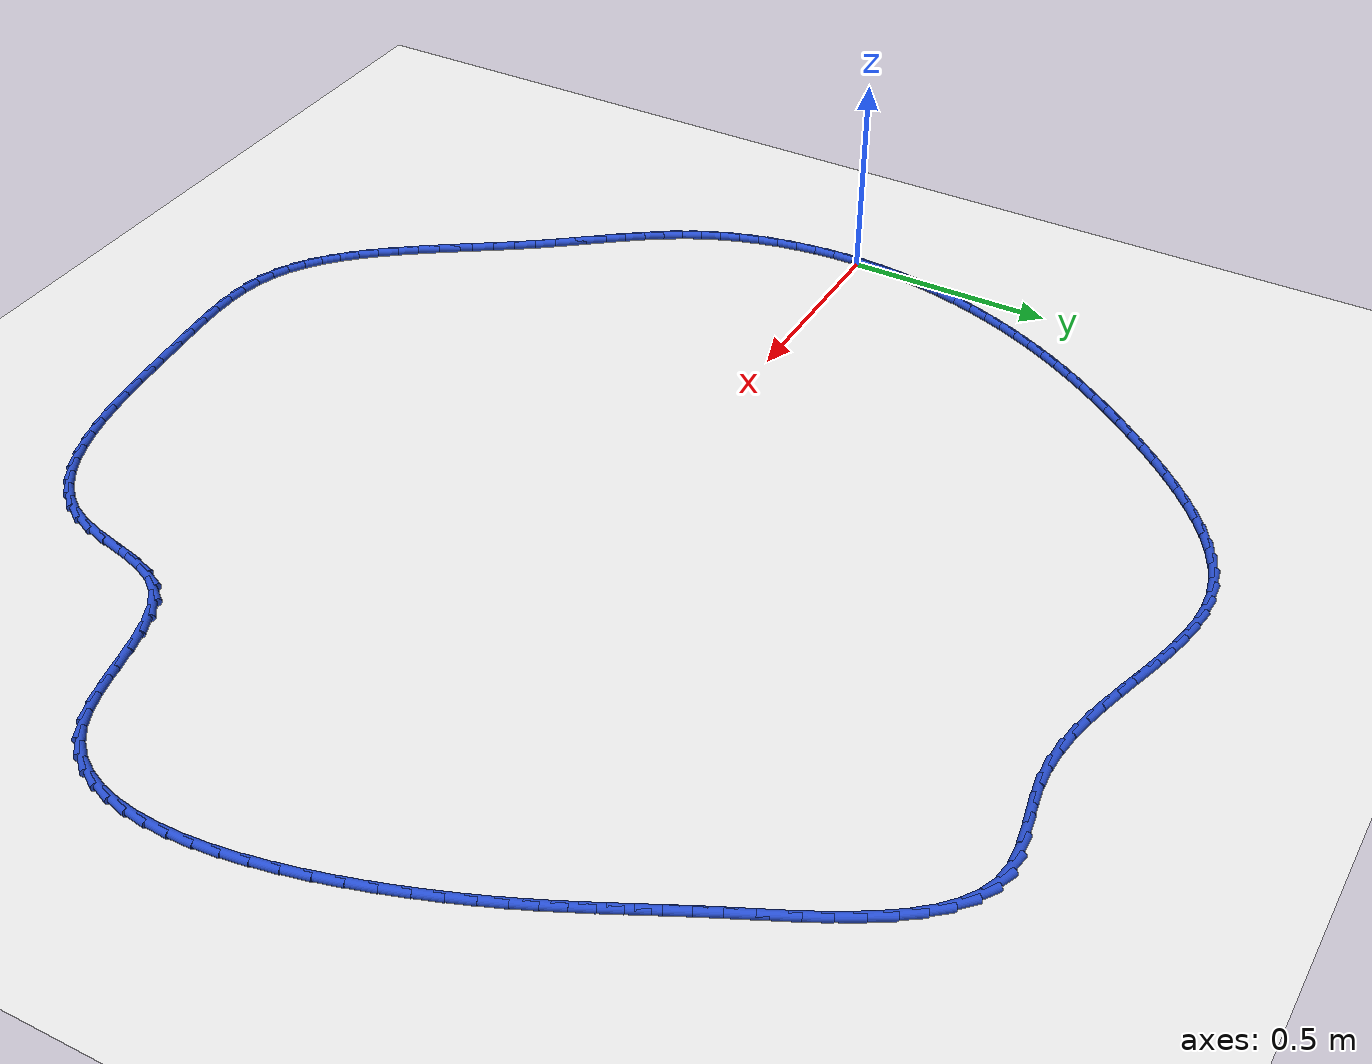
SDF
<sdf version="1.6">
 <world name="default">
  <light name="sun" type="directional">
   <pose>0 0 10 0 -0 0</pose>
   <diffuse>0.8 0.8 0.8 1</diffuse>
   <specular>0.2 0.2 0.2 1</specular>
   <attenuation>
    <range>1000</range>
    <constant>0.9</constant>
    <linear>0.01</linear>
    <quadratic>0.001</quadratic>
   </attenuation>
   <direction>-0.5 0.1 -0.9</direction>
  </light>
  <model name="ground_plane">
   <static>1</static>
   <link name="link">
    <collision name="collision">
     <geometry><plane><normal>0 0 1</normal><size>100 100</size></plane></geometry>
     <surface><friction><ode><mu>100</mu><mu2>50</mu2></ode></friction></surface>
    </collision>
    <visual name="visual">
     <cast_shadows>0</cast_shadows>
     <geometry><plane><normal>0 0 1</normal><size>100 100</size></plane></geometry>
     <material>
      <script><uri>file://media/materials/scripts/gazebo.material</uri><name>Gazebo/WhiteGlow</name></script>
     </material>
    </visual>
   </link>
  </model>
  <gravity>0 0 -9.8</gravity>
  <magnetic_field>6e-06 2.3e-05 -4.2e-05</magnetic_field>
  <atmosphere type="adiabatic"/>
  <physics name="default_physics" default="0" type="ode">
   <max_step_size>0.001</max_step_size>
   <real_time_factor>1</real_time_factor>
   <real_time_update_rate>1000</real_time_update_rate>
  </physics>
  <scene><ambient>0.4 0.4 0.4 1</ambient><background>0.7 0.7 0.7 1</background><shadows>1</shadows></scene>
  <spherical_coordinates>
   <surface_model>EARTH_WGS84</surface_model>
   <latitude_deg>0</latitude_deg>
   <longitude_deg>0</longitude_deg>
   <elevation>0</elevation>
   <heading_deg>0</heading_deg>
  </spherical_coordinates>
  <model name="line">
   <link name="link_0">
    <pose>5.0306980803327406e-17 -2.7755575615628914e-17 0.01 0 1.57 1.5272388991508121</pose>
    <collision name="collision">
     <geometry><cylinder><radius>0.01</radius><length>0.08</length></cylinder></geometry>
    </collision>
    <visual name="visual">
     <material>
      <script><name>Gazebo/Blue</name><uri>file://media/materials/scripts/gazebo.material</uri></script>
     </material>
     <geometry><cylinder><radius>0.01</radius><length>0.08</length></cylinder></geometry>
    </visual>
   </link>
   <link name="link_1">
    <pose>0.002223918584798443 0.05102486726776829 0.01 0 1.57 1.4775595436881013</pose>
    <collision name="collision">
     <geometry><cylinder><radius>0.01</radius><length>0.08</length></cylinder></geometry>
    </collision>
    <visual name="visual">
     <material>
      <script><name>Gazebo/Blue</name><uri>file://media/materials/scripts/gazebo.material</uri></script>
     </material>
     <geometry><cylinder><radius>0.01</radius><length>0.08</length></cylinder></geometry>
    </visual>
   </link>
   <link name="link_2">
    <pose>0.006962776242531 0.10170355599268953 0.01 0 1.57 1.4298396145848786</pose>
    <collision name="collision">
     <geometry><cylinder><radius>0.01</radius><length>0.08</length></cylinder></geometry>
    </collision>
    <visual name="visual">
     <material>
      <script><name>Gazebo/Blue</name><uri>file://media/materials/scripts/gazebo.material</uri></script>
     </material>
     <geometry><cylinder><radius>0.01</radius><length>0.08</length></cylinder></geometry>
    </visual>
   </link>
   <link name="link_3">
    <pose>0.014092496720489735 0.15194903952423786 0.01 0 1.57 1.3840301126188765</pose>
    <collision name="collision">
     <geometry><cylinder><radius>0.01</radius><length>0.08</length></cylinder></geometry>
    </collision>
    <visual name="visual">
     <material>
      <script><name>Gazebo/Blue</name><uri>file://media/materials/scripts/gazebo.material</uri></script>
     </material>
     <geometry><cylinder><radius>0.01</radius><length>0.08</length></cylinder></geometry>
    </visual>
   </link>
   <link name="link_4">
    <pose>0.02348900376596664 0.2016742912118874 0.01 0 1.57 1.3400521082369103</pose>
    <collision name="collision">
     <geometry><cylinder><radius>0.01</radius><length>0.08</length></cylinder></geometry>
    </collision>
    <visual name="visual">
     <material>
      <script><name>Gazebo/Blue</name><uri>file://media/materials/scripts/gazebo.material</uri></script>
     </material>
     <geometry><cylinder><radius>0.01</radius><length>0.08</length></cylinder></geometry>
    </visual>
   </link>
   <link name="link_5">
    <pose>0.03502822112625369 0.25079228440511236 0.01 0 1.57 1.2978026913553944</pose>
    <collision name="collision">
     <geometry><cylinder><radius>0.01</radius><length>0.08</length></cylinder></geometry>
    </collision>
    <visual name="visual">
     <material>
      <script><name>Gazebo/Blue</name><uri>file://media/materials/scripts/gazebo.material</uri></script>
     </material>
     <geometry><cylinder><radius>0.01</radius><length>0.08</length></cylinder></geometry>
    </visual>
   </link>
   <link name="link_6">
    <pose>0.04858607254864292 0.2992159924533869 0.01 0 1.57 1.2571600773190508</pose>
    <collision name="collision">
     <geometry><cylinder><radius>0.01</radius><length>0.08</length></cylinder></geometry>
    </collision>
    <visual name="visual">
     <material>
      <script><name>Gazebo/Blue</name><uri>file://media/materials/scripts/gazebo.material</uri></script>
     </material>
     <geometry><cylinder><radius>0.01</radius><length>0.08</length></cylinder></geometry>
    </visual>
   </link>
   <link name="link_7">
    <pose>0.06403848178042629 0.3468583887061852 0.01 0 1.57 1.2179877338784888</pose>
    <collision name="collision">
     <geometry><cylinder><radius>0.01</radius><length>0.08</length></cylinder></geometry>
    </collision>
    <visual name="visual">
     <material>
      <script><name>Gazebo/Blue</name><uri>file://media/materials/scripts/gazebo.material</uri></script>
     </material>
     <geometry><cylinder><radius>0.01</radius><length>0.08</length></cylinder></geometry>
    </visual>
   </link>
   <link name="link_8">
    <pose>0.08126137256889585 0.39363244651298135 0.01 0 1.57 1.1801067135373107</pose>
    <collision name="collision">
     <geometry><cylinder><radius>0.01</radius><length>0.08</length></cylinder></geometry>
    </collision>
    <visual name="visual">
     <material>
      <script><name>Gazebo/Blue</name><uri>file://media/materials/scripts/gazebo.material</uri></script>
     </material>
     <geometry><cylinder><radius>0.01</radius><length>0.08</length></cylinder></geometry>
    </visual>
   </link>
   <link name="link_9">
    <pose>0.10013675700099565 0.4394619173120163 0.01 0 1.57 1.1431740605714313</pose>
    <collision name="collision">
     <geometry><cylinder><radius>0.01</radius><length>0.08</length></cylinder></geometry>
    </collision>
    <visual name="visual">
     <material>
      <script><name>Gazebo/Blue</name><uri>file://media/materials/scripts/gazebo.material</uri></script>
     </material>
     <geometry><cylinder><radius>0.01</radius><length>0.08</length></cylinder></geometry>
    </visual>
   </link>
   <link name="link_10">
    <pose>0.12060606583139054 0.48437574044359927 0.01 0 1.57 1.1072401756715553</pose>
    <collision name="collision">
     <geometry><cylinder><radius>0.01</radius><length>0.08</length></cylinder></geometry>
    </collision>
    <visual name="visual">
     <material>
      <script><name>Gazebo/Blue</name><uri>file://media/materials/scripts/gazebo.material</uri></script>
     </material>
     <geometry><cylinder><radius>0.01</radius><length>0.08</length></cylinder></geometry>
    </visual>
   </link>
   <link name="link_11">
    <pose>0.14264428056418202 0.5284622495946565 0.01 0 1.57 1.0725524328225868</pose>
    <collision name="collision">
     <geometry><cylinder><radius>0.01</radius><length>0.08</length></cylinder></geometry>
    </collision>
    <visual name="visual">
     <material>
      <script><name>Gazebo/Blue</name><uri>file://media/materials/scripts/gazebo.material</uri></script>
     </material>
     <geometry><cylinder><radius>0.01</radius><length>0.08</length></cylinder></geometry>
    </visual>
   </link>
   <link name="link_12">
    <pose>0.16622676152050464 0.5718104490657525 0.01 0 1.57 1.039331357504351</pose>
    <collision name="collision">
     <geometry><cylinder><radius>0.01</radius><length>0.08</length></cylinder></geometry>
    </collision>
    <visual name="visual">
     <material>
      <script><name>Gazebo/Blue</name><uri>file://media/materials/scripts/gazebo.material</uri></script>
     </material>
     <geometry><cylinder><radius>0.01</radius><length>0.08</length></cylinder></geometry>
    </visual>
   </link>
   <link name="link_13">
    <pose>0.19132886902149296 0.614509343157452 0.01 0 1.57 1.0077643335935016</pose>
    <collision name="collision">
     <geometry><cylinder><radius>0.01</radius><length>0.08</length></cylinder></geometry>
    </collision>
    <visual name="visual">
     <material>
      <script><name>Gazebo/Blue</name><uri>file://media/materials/scripts/gazebo.material</uri></script>
     </material>
     <geometry><cylinder><radius>0.01</radius><length>0.08</length></cylinder></geometry>
    </visual>
   </link>
   <link name="link_14">
    <pose>0.21792596338828174 0.6566479361703199 0.01 0 1.57 0.9780032792882845</pose>
    <collision name="collision">
     <geometry><cylinder><radius>0.01</radius><length>0.08</length></cylinder></geometry>
    </collision>
    <visual name="visual">
     <material>
      <script><name>Gazebo/Blue</name><uri>file://media/materials/scripts/gazebo.material</uri></script>
     </material>
     <geometry><cylinder><radius>0.01</radius><length>0.08</length></cylinder></geometry>
    </visual>
   </link>
   <link name="link_15">
    <pose>0.24599340494200544 0.6983152324049209 0.01 0 1.57 0.9501642488551912</pose>
    <collision name="collision">
     <geometry><cylinder><radius>0.01</radius><length>0.08</length></cylinder></geometry>
    </collision>
    <visual name="visual">
     <material>
      <script><name>Gazebo/Blue</name><uri>file://media/materials/scripts/gazebo.material</uri></script>
     </material>
     <geometry><cylinder><radius>0.01</radius><length>0.08</length></cylinder></geometry>
    </visual>
   </link>
   <link name="link_16">
    <pose>0.27550655400379875 0.73960023616182 0.01 0 1.57 0.9243286719294354</pose>
    <collision name="collision">
     <geometry><cylinder><radius>0.01</radius><length>0.08</length></cylinder></geometry>
    </collision>
    <visual name="visual">
     <material>
      <script><name>Gazebo/Blue</name><uri>file://media/materials/scripts/gazebo.material</uri></script>
     </material>
     <geometry><cylinder><radius>0.01</radius><length>0.08</length></cylinder></geometry>
    </visual>
   </link>
   <link name="link_17">
    <pose>0.3064407708947964 0.7805919517415821 0.01 0 1.57 0.9005458506365052</pose>
    <collision name="collision">
     <geometry><cylinder><radius>0.01</radius><length>0.08</length></cylinder></geometry>
    </collision>
    <visual name="visual">
     <material>
      <script><name>Gazebo/Blue</name><uri>file://media/materials/scripts/gazebo.material</uri></script>
     </material>
     <geometry><cylinder><radius>0.01</radius><length>0.08</length></cylinder></geometry>
    </visual>
   </link>
   <link name="link_18">
    <pose>0.33877141593613286 0.8213793834447715 0.01 0 1.57 0.8788363084535017</pose>
    <collision name="collision">
     <geometry><cylinder><radius>0.01</radius><length>0.08</length></cylinder></geometry>
    </collision>
    <visual name="visual">
     <material>
      <script><name>Gazebo/Blue</name><uri>file://media/materials/scripts/gazebo.material</uri></script>
     </material>
     <geometry><cylinder><radius>0.01</radius><length>0.08</length></cylinder></geometry>
    </visual>
   </link>
   <link name="link_19">
    <pose>0.3724738494489426 0.862051535571953 0.01 0 1.57 0.8582273358059296</pose>
    <collision name="collision">
     <geometry><cylinder><radius>0.01</radius><length>0.08</length></cylinder></geometry>
    </collision>
    <visual name="visual">
     <material>
      <script><name>Gazebo/Blue</name><uri>file://media/materials/scripts/gazebo.material</uri></script>
     </material>
     <geometry><cylinder><radius>0.01</radius><length>0.08</length></cylinder></geometry>
    </visual>
   </link>
   <link name="link_20">
    <pose>0.407519418088347 0.9026132783377154 0.01 0 1.57 0.8335239455667202</pose>
    <collision name="collision">
     <geometry><cylinder><radius>0.01</radius><length>0.08</length></cylinder></geometry>
    </collision>
    <visual name="visual">
     <material>
      <script><name>Gazebo/Blue</name><uri>file://media/materials/scripts/gazebo.material</uri></script>
     </material>
     <geometry><cylinder><radius>0.01</radius><length>0.08</length></cylinder></geometry>
    </visual>
   </link>
   <link name="link_21">
    <pose>0.44385849670834976 0.9426298730523538 0.01 0 1.57 0.8026250250646623</pose>
    <collision name="collision">
     <geometry><cylinder><radius>0.01</radius><length>0.08</length></cylinder></geometry>
    </collision>
    <visual name="visual">
     <material>
      <script><name>Gazebo/Blue</name><uri>file://media/materials/scripts/gazebo.material</uri></script>
     </material>
     <geometry><cylinder><radius>0.01</radius><length>0.08</length></cylinder></geometry>
    </visual>
   </link>
   <link name="link_22">
    <pose>0.48143463312846696 0.9815234733773062 0.01 0 1.57 0.7648076815260989</pose>
    <collision name="collision">
     <geometry><cylinder><radius>0.01</radius><length>0.08</length></cylinder></geometry>
    </collision>
    <visual name="visual">
     <material>
      <script><name>Gazebo/Blue</name><uri>file://media/materials/scripts/gazebo.material</uri></script>
     </material>
     <geometry><cylinder><radius>0.01</radius><length>0.08</length></cylinder></geometry>
    </visual>
   </link>
   <link name="link_23">
    <pose>0.5201913714729116 1.0187161555133943 0.01 0 1.57 0.7190865121437994</pose>
    <collision name="collision">
     <geometry><cylinder><radius>0.01</radius><length>0.08</length></cylinder></geometry>
    </collision>
    <visual name="visual">
     <material>
      <script><name>Gazebo/Blue</name><uri>file://media/materials/scripts/gazebo.material</uri></script>
     </material>
     <geometry><cylinder><radius>0.01</radius><length>0.08</length></cylinder></geometry>
    </visual>
   </link>
   <link name="link_24">
    <pose>0.5600722558658957 1.0536299956614397 0.01 0 1.57 0.6642031032543242</pose>
    <collision name="collision">
     <geometry><cylinder><radius>0.01</radius><length>0.08</length></cylinder></geometry>
    </collision>
    <visual name="visual">
     <material>
      <script><name>Gazebo/Blue</name><uri>file://media/materials/scripts/gazebo.material</uri></script>
     </material>
     <geometry><cylinder><radius>0.01</radius><length>0.08</length></cylinder></geometry>
    </visual>
   </link>
   <link name="link_25">
    <pose>0.601020830431632 1.0856870700222638 0.01 0 1.57 0.5986372614404099</pose>
    <collision name="collision">
     <geometry><cylinder><radius>0.01</radius><length>0.08</length></cylinder></geometry>
    </collision>
    <visual name="visual">
     <material>
      <script><name>Gazebo/Blue</name><uri>file://media/materials/scripts/gazebo.material</uri></script>
     </material>
     <geometry><cylinder><radius>0.01</radius><length>0.08</length></cylinder></geometry>
    </visual>
   </link>
   <link name="link_26">
    <pose>0.6429806392943327 1.114309454796688 0.01 0 1.57 0.5206756706613384</pose>
    <collision name="collision">
     <geometry><cylinder><radius>0.01</radius><length>0.08</length></cylinder></geometry>
    </collision>
    <visual name="visual">
     <material>
      <script><name>Gazebo/Blue</name><uri>file://media/materials/scripts/gazebo.material</uri></script>
     </material>
     <geometry><cylinder><radius>0.01</radius><length>0.08</length></cylinder></geometry>
    </visual>
   </link>
   <link name="link_27">
    <pose>0.6858952265782101 1.1389192261855339 0.01 0 1.57 0.42859819823669854</pose>
    <collision name="collision">
     <geometry><cylinder><radius>0.01</radius><length>0.08</length></cylinder></geometry>
    </collision>
    <visual name="visual">
     <material>
      <script><name>Gazebo/Blue</name><uri>file://media/materials/scripts/gazebo.material</uri></script>
     </material>
     <geometry><cylinder><radius>0.01</radius><length>0.08</length></cylinder></geometry>
    </visual>
   </link>
   <link name="link_28">
    <pose>0.7297081364074769 1.1589384603896227 0.01 0 1.57 0.32106207036278145</pose>
    <collision name="collision">
     <geometry><cylinder><radius>0.01</radius><length>0.08</length></cylinder></geometry>
    </collision>
    <visual name="visual">
     <material>
      <script><name>Gazebo/Blue</name><uri>file://media/materials/scripts/gazebo.material</uri></script>
     </material>
     <geometry><cylinder><radius>0.01</radius><length>0.08</length></cylinder></geometry>
    </visual>
   </link>
   <link name="link_29">
    <pose>0.7743629129063457 1.1737892336097768 0.01 0 1.57 0.19778036031494722</pose>
    <collision name="collision">
     <geometry><cylinder><radius>0.01</radius><length>0.08</length></cylinder></geometry>
    </collision>
    <visual name="visual">
     <material>
      <script><name>Gazebo/Blue</name><uri>file://media/materials/scripts/gazebo.material</uri></script>
     </material>
     <geometry><cylinder><radius>0.01</radius><length>0.08</length></cylinder></geometry>
    </visual>
   </link>
   <link name="link_30">
    <pose>0.8198031244990173 1.1828954621599586 0.01 0 1.57 0.06905127401093203</pose>
    <collision name="collision">
     <geometry><cylinder><radius>0.01</radius><length>0.08</length></cylinder></geometry>
    </collision>
    <visual name="visual">
     <material>
      <script><name>Gazebo/Blue</name><uri>file://media/materials/scripts/gazebo.material</uri></script>
     </material>
     <geometry><cylinder><radius>0.01</radius><length>0.08</length></cylinder></geometry>
    </visual>
   </link>
   <link name="link_31">
    <pose>0.8659777261118524 1.1860889544496456 0.01 0 1.57 -0.04197397387465293</pose>
    <collision name="collision">
     <geometry><cylinder><radius>0.01</radius><length>0.08</length></cylinder></geometry>
    </collision>
    <visual name="visual">
     <material>
      <script><name>Gazebo/Blue</name><uri>file://media/materials/scripts/gazebo.material</uri></script>
     </material>
     <geometry><cylinder><radius>0.01</radius><length>0.08</length></cylinder></geometry>
    </visual>
   </link>
   <link name="link_32">
    <pose>0.9128478081291671 1.1841204746836906 0.01 0 1.57 -0.13083217703381197</pose>
    <collision name="collision">
     <geometry><cylinder><radius>0.01</radius><length>0.08</length></cylinder></geometry>
    </collision>
    <visual name="visual">
     <material>
      <script><name>Gazebo/Blue</name><uri>file://media/materials/scripts/gazebo.material</uri></script>
     </material>
     <geometry><cylinder><radius>0.01</radius><length>0.08</length></cylinder></geometry>
    </visual>
   </link>
   <link name="link_33">
    <pose>0.9603761213020608 1.1778665181010528 0.01 0 1.57 -0.19805606097018524</pose>
    <collision name="collision">
     <geometry><cylinder><radius>0.01</radius><length>0.08</length></cylinder></geometry>
    </collision>
    <visual name="visual">
     <material>
      <script><name>Gazebo/Blue</name><uri>file://media/materials/scripts/gazebo.material</uri></script>
     </material>
     <geometry><cylinder><radius>0.01</radius><length>0.08</length></cylinder></geometry>
    </visual>
   </link>
   <link name="link_34">
    <pose>1.008525416381634 1.1682035799406898 0.01 0 1.57 -0.2452136403749122</pose>
    <collision name="collision">
     <geometry><cylinder><radius>0.01</radius><length>0.08</length></cylinder></geometry>
    </collision>
    <visual name="visual">
     <material>
      <script><name>Gazebo/Blue</name><uri>file://media/materials/scripts/gazebo.material</uri></script>
     </material>
     <geometry><cylinder><radius>0.01</radius><length>0.08</length></cylinder></geometry>
    </visual>
   </link>
   <link name="link_35">
    <pose>1.0572584441189854 1.1560081554415593 0.01 0 1.57 -0.274008600614039</pose>
    <collision name="collision">
     <geometry><cylinder><radius>0.01</radius><length>0.08</length></cylinder></geometry>
    </collision>
    <visual name="visual">
     <material>
      <script><name>Gazebo/Blue</name><uri>file://media/materials/scripts/gazebo.material</uri></script>
     </material>
     <geometry><cylinder><radius>0.01</radius><length>0.08</length></cylinder></geometry>
    </visual>
   </link>
   <link name="link_36">
    <pose>1.106537955265216 1.1421567398426198 0.01 0 1.57 -0.28581412066753836</pose>
    <collision name="collision">
     <geometry><cylinder><radius>0.01</radius><length>0.08</length></cylinder></geometry>
    </collision>
    <visual name="visual">
     <material>
      <script><name>Gazebo/Blue</name><uri>file://media/materials/scripts/gazebo.material</uri></script>
     </material>
     <geometry><cylinder><radius>0.01</radius><length>0.08</length></cylinder></geometry>
    </visual>
   </link>
   <link name="link_37">
    <pose>1.156326700571424 1.1275258283828284 0.01 0 1.57 -0.2814919471599445</pose>
    <collision name="collision">
     <geometry><cylinder><radius>0.01</radius><length>0.08</length></cylinder></geometry>
    </collision>
    <visual name="visual">
     <material>
      <script><name>Gazebo/Blue</name><uri>file://media/materials/scripts/gazebo.material</uri></script>
     </material>
     <geometry><cylinder><radius>0.01</radius><length>0.08</length></cylinder></geometry>
    </visual>
   </link>
   <link name="link_38">
    <pose>1.2065874307887097 1.1129919163011437 0.01 0 1.57 -0.26136883156408985</pose>
    <collision name="collision">
     <geometry><cylinder><radius>0.01</radius><length>0.08</length></cylinder></geometry>
    </collision>
    <visual name="visual">
     <material>
      <script><name>Gazebo/Blue</name><uri>file://media/materials/scripts/gazebo.material</uri></script>
     </material>
     <geometry><cylinder><radius>0.01</radius><length>0.08</length></cylinder></geometry>
    </visual>
   </link>
   <link name="link_39">
    <pose>1.257282896668173 1.0994314988365235 0.01 0 1.57 -0.225307016189881</pose>
    <collision name="collision">
     <geometry><cylinder><radius>0.01</radius><length>0.08</length></cylinder></geometry>
    </collision>
    <visual name="visual">
     <material>
      <script><name>Gazebo/Blue</name><uri>file://media/materials/scripts/gazebo.material</uri></script>
     </material>
     <geometry><cylinder><radius>0.01</radius><length>0.08</length></cylinder></geometry>
    </visual>
   </link>
   <link name="link_40">
    <pose>1.3083758489609136 1.0877210712279257 0.01 0 1.57 -0.17286159300284804</pose>
    <collision name="collision">
     <geometry><cylinder><radius>0.01</radius><length>0.08</length></cylinder></geometry>
    </collision>
    <visual name="visual">
     <material>
      <script><name>Gazebo/Blue</name><uri>file://media/materials/scripts/gazebo.material</uri></script>
     </material>
     <geometry><cylinder><radius>0.01</radius><length>0.08</length></cylinder></geometry>
    </visual>
   </link>
   <link name="link_41">
    <pose>1.3598290384180318 1.0787371287143084 0.01 0 1.57 -0.10355561114296845</pose>
    <collision name="collision">
     <geometry><cylinder><radius>0.01</radius><length>0.08</length></cylinder></geometry>
    </collision>
    <visual name="visual">
     <material>
      <script><name>Gazebo/Blue</name><uri>file://media/materials/scripts/gazebo.material</uri></script>
     </material>
     <geometry><cylinder><radius>0.01</radius><length>0.08</length></cylinder></geometry>
    </visual>
   </link>
   <link name="link_42">
    <pose>1.411605215790626 1.0733561665346292 0.01 0 1.57 -0.017313932973075225</pose>
    <collision name="collision">
     <geometry><cylinder><radius>0.01</radius><length>0.08</length></cylinder></geometry>
    </collision>
    <visual name="visual">
     <material>
      <script><name>Gazebo/Blue</name><uri>file://media/materials/scripts/gazebo.material</uri></script>
     </material>
     <geometry><cylinder><radius>0.01</radius><length>0.08</length></cylinder></geometry>
    </visual>
   </link>
   <link name="link_43">
    <pose>1.4636671318297965 1.0724546799278465 0.01 0 1.57 0.08406274976963503</pose>
    <collision name="collision">
     <geometry><cylinder><radius>0.01</radius><length>0.08</length></cylinder></geometry>
    </collision>
    <visual name="visual">
     <material>
      <script><name>Gazebo/Blue</name><uri>file://media/materials/scripts/gazebo.material</uri></script>
     </material>
     <geometry><cylinder><radius>0.01</radius><length>0.08</length></cylinder></geometry>
    </visual>
   </link>
   <link name="link_44">
    <pose>1.5159696839445798 1.0768617621219103 0.01 0 1.57 0.1667311757712632</pose>
    <collision name="collision">
     <geometry><cylinder><radius>0.01</radius><length>0.08</length></cylinder></geometry>
    </collision>
    <visual name="visual">
     <material>
      <script><name>Gazebo/Blue</name><uri>file://media/materials/scripts/gazebo.material</uri></script>
     </material>
     <geometry><cylinder><radius>0.01</radius><length>0.08</length></cylinder></geometry>
    </visual>
   </link>
   <link name="link_45">
    <pose>1.5681763979310692 1.085647815548833 0.01 0 1.57 0.19210658688101442</pose>
    <collision name="collision">
     <geometry><cylinder><radius>0.01</radius><length>0.08</length></cylinder></geometry>
    </collision>
    <visual name="visual">
     <material>
      <script><name>Gazebo/Blue</name><uri>file://media/materials/scripts/gazebo.material</uri></script>
     </material>
     <geometry><cylinder><radius>0.01</radius><length>0.08</length></cylinder></geometry>
    </visual>
   </link>
   <link name="link_46">
    <pose>1.6195801630850977 1.0956461166726625 0.01 0 1.57 0.15708765076795267</pose>
    <collision name="collision">
     <geometry><cylinder><radius>0.01</radius><length>0.08</length></cylinder></geometry>
    </collision>
    <visual name="visual">
     <material>
      <script><name>Gazebo/Blue</name><uri>file://media/materials/scripts/gazebo.material</uri></script>
     </material>
     <geometry><cylinder><radius>0.01</radius><length>0.08</length></cylinder></geometry>
    </visual>
   </link>
   <link name="link_47">
    <pose>1.6694498740945471 1.1035451128310498 0.01 0 1.57 0.052219303408299445</pose>
    <collision name="collision">
     <geometry><cylinder><radius>0.01</radius><length>0.08</length></cylinder></geometry>
    </collision>
    <visual name="visual">
     <material>
      <script><name>Gazebo/Blue</name><uri>file://media/materials/scripts/gazebo.material</uri></script>
     </material>
     <geometry><cylinder><radius>0.01</radius><length>0.08</length></cylinder></geometry>
    </visual>
   </link>
   <link name="link_48">
    <pose>1.7170544256472982 1.1060332513616447 0.01 0 1.57 -0.1376543515479821</pose>
    <collision name="collision">
     <geometry><cylinder><radius>0.01</radius><length>0.08</length></cylinder></geometry>
    </collision>
    <visual name="visual">
     <material>
      <script><name>Gazebo/Blue</name><uri>file://media/materials/scripts/gazebo.material</uri></script>
     </material>
     <geometry><cylinder><radius>0.01</radius><length>0.08</length></cylinder></geometry>
    </visual>
   </link>
   <link name="link_49">
    <pose>1.7616743188051753 1.0998520374624046 0.01 0 1.57 -0.37274357385876616</pose>
    <collision name="collision">
     <geometry><cylinder><radius>0.01</radius><length>0.08</length></cylinder></geometry>
    </collision>
    <visual name="visual">
     <material>
      <script><name>Gazebo/Blue</name><uri>file://media/materials/scripts/gazebo.material</uri></script>
     </material>
     <geometry><cylinder><radius>0.01</radius><length>0.08</length></cylinder></geometry>
    </visual>
   </link>
   <link name="link_50">
    <pose>1.8030152614643125 1.0836867845289722 0.01 0 1.57 -0.5783365354380466</pose>
    <collision name="collision">
     <geometry><cylinder><radius>0.01</radius><length>0.08</length></cylinder></geometry>
    </collision>
    <visual name="visual">
     <material>
      <script><name>Gazebo/Blue</name><uri>file://media/materials/scripts/gazebo.material</uri></script>
     </material>
     <geometry><cylinder><radius>0.01</radius><length>0.08</length></cylinder></geometry>
    </visual>
   </link>
   <link name="link_51">
    <pose>1.8413207374968203 1.0586812174082412 0.01 0 1.57 -0.7413159635463125</pose>
    <collision name="collision">
     <geometry><cylinder><radius>0.01</radius><length>0.08</length></cylinder></geometry>
    </collision>
    <visual name="visual">
     <material>
      <script><name>Gazebo/Blue</name><uri>file://media/materials/scripts/gazebo.material</uri></script>
     </material>
     <geometry><cylinder><radius>0.01</radius><length>0.08</length></cylinder></geometry>
    </visual>
   </link>
   <link name="link_52">
    <pose>1.8768687410049314 1.026136822447635 0.01 0 1.57 -0.8647467379044604</pose>
    <collision name="collision">
     <geometry><cylinder><radius>0.01</radius><length>0.08</length></cylinder></geometry>
    </collision>
    <visual name="visual">
     <material>
      <script><name>Gazebo/Blue</name><uri>file://media/materials/scripts/gazebo.material</uri></script>
     </material>
     <geometry><cylinder><radius>0.01</radius><length>0.08</length></cylinder></geometry>
    </visual>
   </link>
   <link name="link_53">
    <pose>1.9099372660908787 0.9873550859945773 0.01 0 1.57 -0.9560178994460585</pose>
    <collision name="collision">
     <geometry><cylinder><radius>0.01</radius><length>0.08</length></cylinder></geometry>
    </collision>
    <visual name="visual">
     <material>
      <script><name>Gazebo/Blue</name><uri>file://media/materials/scripts/gazebo.material</uri></script>
     </material>
     <geometry><cylinder><radius>0.01</radius><length>0.08</length></cylinder></geometry>
    </visual>
   </link>
   <link name="link_54">
    <pose>1.9408043068568945 0.9436374943964908 0.01 0 1.57 -1.0221509611254789</pose>
    <collision name="collision">
     <geometry><cylinder><radius>0.01</radius><length>0.08</length></cylinder></geometry>
    </collision>
    <visual name="visual">
     <material>
      <script><name>Gazebo/Blue</name><uri>file://media/materials/scripts/gazebo.material</uri></script>
     </material>
     <geometry><cylinder><radius>0.01</radius><length>0.08</length></cylinder></geometry>
    </visual>
   </link>
   <link name="link_55">
    <pose>1.9697478574052119 0.8962855340008001 0.01 0 1.57 -1.0683953055606403</pose>
    <collision name="collision">
     <geometry><cylinder><radius>0.01</radius><length>0.08</length></cylinder></geometry>
    </collision>
    <visual name="visual">
     <material>
      <script><name>Gazebo/Blue</name><uri>file://media/materials/scripts/gazebo.material</uri></script>
     </material>
     <geometry><cylinder><radius>0.01</radius><length>0.08</length></cylinder></geometry>
    </visual>
   </link>
   <link name="link_56">
    <pose>1.997045911838063 0.8466006911549279 0.01 0 1.57 -1.0981599629457697</pose>
    <collision name="collision">
     <geometry><cylinder><radius>0.01</radius><length>0.08</length></cylinder></geometry>
    </collision>
    <visual name="visual">
     <material>
      <script><name>Gazebo/Blue</name><uri>file://media/materials/scripts/gazebo.material</uri></script>
     </material>
     <geometry><cylinder><radius>0.01</radius><length>0.08</length></cylinder></geometry>
    </visual>
   </link>
   <link name="link_57">
    <pose>2.022976464257681 0.7958844522062977 0.01 0 1.57 -1.113225469356338</pose>
    <collision name="collision">
     <geometry><cylinder><radius>0.01</radius><length>0.08</length></cylinder></geometry>
    </collision>
    <visual name="visual">
     <material>
      <script><name>Gazebo/Blue</name><uri>file://media/materials/scripts/gazebo.material</uri></script>
     </material>
     <geometry><cylinder><radius>0.01</radius><length>0.08</length></cylinder></geometry>
    </visual>
   </link>
   <link name="link_58">
    <pose>2.047817508766299 0.7454383035023329 0.01 0 1.57 -1.1138521939577677</pose>
    <collision name="collision">
     <geometry><cylinder><radius>0.01</radius><length>0.08</length></cylinder></geometry>
    </collision>
    <visual name="visual">
     <material>
      <script><name>Gazebo/Blue</name><uri>file://media/materials/scripts/gazebo.material</uri></script>
     </material>
     <geometry><cylinder><radius>0.01</radius><length>0.08</length></cylinder></geometry>
    </visual>
   </link>
   <link name="link_59">
    <pose>2.071846967642852 0.6965630240749457 0.01 0 1.57 -1.1036554198427984</pose>
    <collision name="collision">
     <geometry><cylinder><radius>0.01</radius><length>0.08</length></cylinder></geometry>
    </collision>
    <visual name="visual">
     <material>
      <script><name>Gazebo/Blue</name><uri>file://media/materials/scripts/gazebo.material</uri></script>
     </material>
     <geometry><cylinder><radius>0.01</radius><length>0.08</length></cylinder></geometry>
    </visual>
   </link>
   <link name="link_60">
    <pose>2.0952937027569027 0.6500762462642672 0.01 0 1.57 -1.095450552324791</pose>
    <collision name="collision">
     <geometry><cylinder><radius>0.01</radius><length>0.08</length></cylinder></geometry>
    </collision>
    <visual name="visual">
     <material>
      <script><name>Gazebo/Blue</name><uri>file://media/materials/scripts/gazebo.material</uri></script>
     </material>
     <geometry><cylinder><radius>0.01</radius><length>0.08</length></cylinder></geometry>
    </visual>
   </link>
   <link name="link_61">
    <pose>2.1182521324573647 0.6054716032211329 0.01 0 1.57 -1.0922589274482102</pose>
    <collision name="collision">
     <geometry><cylinder><radius>0.01</radius><length>0.08</length></cylinder></geometry>
    </collision>
    <visual name="visual">
     <material>
      <script><name>Gazebo/Blue</name><uri>file://media/materials/scripts/gazebo.material</uri></script>
     </material>
     <geometry><cylinder><radius>0.01</radius><length>0.08</length></cylinder></geometry>
    </visual>
   </link>
   <link name="link_62">
    <pose>2.14079385123869 0.5620179588798645 0.01 0 1.57 -1.0945928406013012</pose>
    <collision name="collision">
     <geometry><cylinder><radius>0.01</radius><length>0.08</length></cylinder></geometry>
    </collision>
    <visual name="visual">
     <material>
      <script><name>Gazebo/Blue</name><uri>file://media/materials/scripts/gazebo.material</uri></script>
     </material>
     <geometry><cylinder><radius>0.01</radius><length>0.08</length></cylinder></geometry>
    </visual>
   </link>
   <link name="link_63">
    <pose>2.162990453595331 0.5189841771747844 0.01 0 1.57 -1.1025350777787553</pose>
    <collision name="collision">
     <geometry><cylinder><radius>0.01</radius><length>0.08</length></cylinder></geometry>
    </collision>
    <visual name="visual">
     <material>
      <script><name>Gazebo/Blue</name><uri>file://media/materials/scripts/gazebo.material</uri></script>
     </material>
     <geometry><cylinder><radius>0.01</radius><length>0.08</length></cylinder></geometry>
    </visual>
   </link>
   <link name="link_64">
    <pose>2.1849135340217405 0.475639122040214 0.01 0 1.57 -1.115702284388976</pose>
    <collision name="collision">
     <geometry><cylinder><radius>0.01</radius><length>0.08</length></cylinder></geometry>
    </collision>
    <visual name="visual">
     <material>
      <script><name>Gazebo/Blue</name><uri>file://media/materials/scripts/gazebo.material</uri></script>
     </material>
     <geometry><cylinder><radius>0.01</radius><length>0.08</length></cylinder></geometry>
    </visual>
   </link>
   <link name="link_65">
    <pose>2.2066346870123676 0.431251657410475 0.01 0 1.57 -1.1332975785269375</pose>
    <collision name="collision">
     <geometry><cylinder><radius>0.01</radius><length>0.08</length></cylinder></geometry>
    </collision>
    <visual name="visual">
     <material>
      <script><name>Gazebo/Blue</name><uri>file://media/materials/scripts/gazebo.material</uri></script>
     </material>
     <geometry><cylinder><radius>0.01</radius><length>0.08</length></cylinder></geometry>
    </visual>
   </link>
   <link name="link_66">
    <pose>2.228225507061668 0.3850906472198897 0.01 0 1.57 -1.1542390359426522</pose>
    <collision name="collision">
     <geometry><cylinder><radius>0.01</radius><length>0.08</length></cylinder></geometry>
    </collision>
    <visual name="visual">
     <material>
      <script><name>Gazebo/Blue</name><uri>file://media/materials/scripts/gazebo.material</uri></script>
     </material>
     <geometry><cylinder><radius>0.01</radius><length>0.08</length></cylinder></geometry>
    </visual>
   </link>
   <link name="link_67">
    <pose>2.249757440930759 0.33642536569932047 0.01 0 1.57 -1.1770635725032588</pose>
    <collision name="collision">
     <geometry><cylinder><radius>0.01</radius><length>0.08</length></cylinder></geometry>
    </collision>
    <visual name="visual">
     <material>
      <script><name>Gazebo/Blue</name><uri>file://media/materials/scripts/gazebo.material</uri></script>
     </material>
     <geometry><cylinder><radius>0.01</radius><length>0.08</length></cylinder></geometry>
    </visual>
   </link>
   <link name="link_68">
    <pose>2.2711966729316635 0.2848174301692055 0.01 0 1.57 -1.2006853644421709</pose>
    <collision name="collision">
     <geometry><cylinder><radius>0.01</radius><length>0.08</length></cylinder></geometry>
    </collision>
    <visual name="visual">
     <material>
      <script><name>Gazebo/Blue</name><uri>file://media/materials/scripts/gazebo.material</uri></script>
     </material>
     <geometry><cylinder><radius>0.01</radius><length>0.08</length></cylinder></geometry>
    </visual>
   </link>
   <link name="link_69">
    <pose>2.292219256159351 0.230634233011282 0.01 0 1.57 -1.2255367192810869</pose>
    <collision name="collision">
     <geometry><cylinder><radius>0.01</radius><length>0.08</length></cylinder></geometry>
    </collision>
    <visual name="visual">
     <material>
      <script><name>Gazebo/Blue</name><uri>file://media/materials/scripts/gazebo.material</uri></script>
     </material>
     <geometry><cylinder><radius>0.01</radius><length>0.08</length></cylinder></geometry>
    </visual>
   </link>
   <link name="link_70">
    <pose>2.3124516849807253 0.1743808049750319 0.01 0 1.57 -1.2522262469200827</pose>
    <collision name="collision">
     <geometry><cylinder><radius>0.01</radius><length>0.08</length></cylinder></geometry>
    </collision>
    <visual name="visual">
     <material>
      <script><name>Gazebo/Blue</name><uri>file://media/materials/scripts/gazebo.material</uri></script>
     </material>
     <geometry><cylinder><radius>0.01</radius><length>0.08</length></cylinder></geometry>
    </visual>
   </link>
   <link name="link_71">
    <pose>2.331520453762689 0.11656217680993676 0.01 0 1.57 -1.281398146462841</pose>
    <collision name="collision">
     <geometry><cylinder><radius>0.01</radius><length>0.08</length></cylinder></geometry>
    </collision>
    <visual name="visual">
     <material>
      <script><name>Gazebo/Blue</name><uri>file://media/materials/scripts/gazebo.material</uri></script>
     </material>
     <geometry><cylinder><radius>0.01</radius><length>0.08</length></cylinder></geometry>
    </visual>
   </link>
   <link name="link_72">
    <pose>2.3490520568721465 0.05768337926547948 0.01 0 1.57 -1.3137807053818664</pose>
    <collision name="collision">
     <geometry><cylinder><radius>0.01</radius><length>0.08</length></cylinder></geometry>
    </collision>
    <visual name="visual">
     <material>
      <script><name>Gazebo/Blue</name><uri>file://media/materials/scripts/gazebo.material</uri></script>
     </material>
     <geometry><cylinder><radius>0.01</radius><length>0.08</length></cylinder></geometry>
    </visual>
   </link>
   <link name="link_73">
    <pose>2.364672988675998 -0.001750556908858586 0.01 0 1.57 -1.3502365484249814</pose>
    <collision name="collision">
     <geometry><cylinder><radius>0.01</radius><length>0.08</length></cylinder></geometry>
    </collision>
    <visual name="visual">
     <material>
      <script><name>Gazebo/Blue</name><uri>file://media/materials/scripts/gazebo.material</uri></script>
     </material>
     <geometry><cylinder><radius>0.01</radius><length>0.08</length></cylinder></geometry>
    </visual>
   </link>
   <link name="link_74">
    <pose>2.378009743541148 -0.061234600963595356 0.01 0 1.57 -1.391820217604714</pose>
    <collision name="collision">
     <geometry><cylinder><radius>0.01</radius><length>0.08</length></cylinder></geometry>
    </collision>
    <visual name="visual">
     <material>
      <script><name>Gazebo/Blue</name><uri>file://media/materials/scripts/gazebo.material</uri></script>
     </material>
     <geometry><cylinder><radius>0.01</radius><length>0.08</length></cylinder></geometry>
    </visual>
   </link>
   <link name="link_75">
    <pose>2.3886888158345 -0.12026372214924898 0.01 0 1.57 -1.4398469825482207</pose>
    <collision name="collision">
     <geometry><cylinder><radius>0.01</radius><length>0.08</length></cylinder></geometry>
    </collision>
    <visual name="visual">
     <material>
      <script><name>Gazebo/Blue</name><uri>file://media/materials/scripts/gazebo.material</uri></script>
     </material>
     <geometry><cylinder><radius>0.01</radius><length>0.08</length></cylinder></geometry>
    </visual>
   </link>
   <link name="link_76">
    <pose>2.396336699922956 -0.17833288971633787 0.01 0 1.57 -1.4959737840576777</pose>
    <collision name="collision">
     <geometry><cylinder><radius>0.01</radius><length>0.08</length></cylinder></geometry>
    </collision>
    <visual name="visual">
     <material>
      <script><name>Gazebo/Blue</name><uri>file://media/materials/scripts/gazebo.material</uri></script>
     </material>
     <geometry><cylinder><radius>0.01</radius><length>0.08</length></cylinder></geometry>
    </visual>
   </link>
   <link name="link_77">
    <pose>2.4005798901734186 -0.2349370729153797 0.01 0 1.57 -1.5622855437320609</pose>
    <collision name="collision">
     <geometry><cylinder><radius>0.01</radius><length>0.08</length></cylinder></geometry>
    </collision>
    <visual name="visual">
     <material>
      <script><name>Gazebo/Blue</name><uri>file://media/materials/scripts/gazebo.material</uri></script>
     </material>
     <geometry><cylinder><radius>0.01</radius><length>0.08</length></cylinder></geometry>
    </visual>
   </link>
   <link name="link_78">
    <pose>2.401044880952792 -0.2895712409968915 0.01 0 1.57 1.5002316210398952</pose>
    <collision name="collision">
     <geometry><cylinder><radius>0.01</radius><length>0.08</length></cylinder></geometry>
    </collision>
    <visual name="visual">
     <material>
      <script><name>Gazebo/Blue</name><uri>file://media/materials/scripts/gazebo.material</uri></script>
     </material>
     <geometry><cylinder><radius>0.01</radius><length>0.08</length></cylinder></geometry>
    </visual>
   </link>
   <link name="link_79">
    <pose>2.3973581666279786 -0.3417303632113934 0.01 0 1.57 1.4053426411994847</pose>
    <collision name="collision">
     <geometry><cylinder><radius>0.01</radius><length>0.08</length></cylinder></geometry>
    </collision>
    <visual name="visual">
     <material>
      <script><name>Gazebo/Blue</name><uri>file://media/materials/scripts/gazebo.material</uri></script>
     </material>
     <geometry><cylinder><radius>0.01</radius><length>0.08</length></cylinder></geometry>
    </visual>
   </link>
   <link name="link_80">
    <pose>2.3891462415658813 -0.39090940880940134 0.01 0 1.57 1.2913795425973227</pose>
    <collision name="collision">
     <geometry><cylinder><radius>0.01</radius><length>0.08</length></cylinder></geometry>
    </collision>
    <visual name="visual">
     <material>
      <script><name>Gazebo/Blue</name><uri>file://media/materials/scripts/gazebo.material</uri></script>
     </material>
     <geometry><cylinder><radius>0.01</radius><length>0.08</length></cylinder></geometry>
    </visual>
   </link>
   <link name="link_81">
    <pose>2.376035600133402 -0.43660334704143533 0.01 0 1.57 1.155622855037631</pose>
    <collision name="collision">
     <geometry><cylinder><radius>0.01</radius><length>0.08</length></cylinder></geometry>
    </collision>
    <visual name="visual">
     <material>
      <script><name>Gazebo/Blue</name><uri>file://media/materials/scripts/gazebo.material</uri></script>
     </material>
     <geometry><cylinder><radius>0.01</radius><length>0.08</length></cylinder></geometry>
    </visual>
   </link>
   <link name="link_82">
    <pose>2.3576527366974456 -0.47830714715801237 0.01 0 1.57 0.9973934146492227</pose>
    <collision name="collision">
     <geometry><cylinder><radius>0.01</radius><length>0.08</length></cylinder></geometry>
    </collision>
    <visual name="visual">
     <material>
      <script><name>Gazebo/Blue</name><uri>file://media/materials/scripts/gazebo.material</uri></script>
     </material>
     <geometry><cylinder><radius>0.01</radius><length>0.08</length></cylinder></geometry>
    </visual>
   </link>
   <link name="link_83">
    <pose>2.3336241456249143 -0.5155157784096499 0.01 0 1.57 0.8200893031991454</pose>
    <collision name="collision">
     <geometry><cylinder><radius>0.01</radius><length>0.08</length></cylinder></geometry>
    </collision>
    <visual name="visual">
     <material>
      <script><name>Gazebo/Blue</name><uri>file://media/materials/scripts/gazebo.material</uri></script>
     </material>
     <geometry><cylinder><radius>0.01</radius><length>0.08</length></cylinder></geometry>
    </visual>
   </link>
   <link name="link_84">
    <pose>2.3035763212827094 -0.5477242100468672 0.01 0 1.57 0.6323940080478144</pose>
    <collision name="collision">
     <geometry><cylinder><radius>0.01</radius><length>0.08</length></cylinder></geometry>
    </collision>
    <visual name="visual">
     <material>
      <script><name>Gazebo/Blue</name><uri>file://media/materials/scripts/gazebo.material</uri></script>
     </material>
     <geometry><cylinder><radius>0.01</radius><length>0.08</length></cylinder></geometry>
    </visual>
   </link>
   <link name="link_85">
    <pose>2.267135758037738 -0.5744274113201818 0.01 0 1.57 0.4510348395678551</pose>
    <collision name="collision">
     <geometry><cylinder><radius>0.01</radius><length>0.08</length></cylinder></geometry>
    </collision>
    <visual name="visual">
     <material>
      <script><name>Gazebo/Blue</name><uri>file://media/materials/scripts/gazebo.material</uri></script>
     </material>
     <geometry><cylinder><radius>0.01</radius><length>0.08</length></cylinder></geometry>
    </visual>
   </link>
   <link name="link_86">
    <pose>2.224087384193141 -0.5952771169971801 0.01 0 1.57 0.321141715732066</pose>
    <collision name="collision">
     <geometry><cylinder><radius>0.01</radius><length>0.08</length></cylinder></geometry>
    </collision>
    <visual name="visual">
     <material>
      <script><name>Gazebo/Blue</name><uri>file://media/materials/scripts/gazebo.material</uri></script>
     </material>
     <geometry><cylinder><radius>0.01</radius><length>0.08</length></cylinder></geometry>
    </visual>
   </link>
   <link name="link_87">
    <pose>2.1756850321788646 -0.6113784973935517 0.01 0 1.57 0.25078579016365227</pose>
    <collision name="collision">
     <geometry><cylinder><radius>0.01</radius><length>0.08</length></cylinder></geometry>
    </collision>
    <visual name="visual">
     <material>
      <script><name>Gazebo/Blue</name><uri>file://media/materials/scripts/gazebo.material</uri></script>
     </material>
     <geometry><cylinder><radius>0.01</radius><length>0.08</length></cylinder></geometry>
    </visual>
   </link>
   <link name="link_88">
    <pose>2.1239787605830944 -0.624624564169842 0.01 0 1.57 0.22808580606963388</pose>
    <collision name="collision">
     <geometry><cylinder><radius>0.01</radius><length>0.08</length></cylinder></geometry>
    </collision>
    <visual name="visual">
     <material>
      <script><name>Gazebo/Blue</name><uri>file://media/materials/scripts/gazebo.material</uri></script>
     </material>
     <geometry><cylinder><radius>0.01</radius><length>0.08</length></cylinder></geometry>
    </visual>
   </link>
   <link name="link_89">
    <pose>2.071026497023882 -0.6369161151501216 0.01 0 1.57 0.24863512679720598</pose>
    <collision name="collision">
     <geometry><cylinder><radius>0.01</radius><length>0.08</length></cylinder></geometry>
    </collision>
    <visual name="visual">
     <material>
      <script><name>Gazebo/Blue</name><uri>file://media/materials/scripts/gazebo.material</uri></script>
     </material>
     <geometry><cylinder><radius>0.01</radius><length>0.08</length></cylinder></geometry>
    </visual>
   </link>
   <link name="link_90">
    <pose>2.0188861691192757 -0.6501539481584594 0.01 0 1.57 0.315553263761147</pose>
    <collision name="collision">
     <geometry><cylinder><radius>0.01</radius><length>0.08</length></cylinder></geometry>
    </collision>
    <visual name="visual">
     <material>
      <script><name>Gazebo/Blue</name><uri>file://media/materials/scripts/gazebo.material</uri></script>
     </material>
     <geometry><cylinder><radius>0.01</radius><length>0.08</length></cylinder></geometry>
    </visual>
   </link>
   <link name="link_91">
    <pose>1.9696157044873275 -0.6662388610189253 0.01 0 1.57 0.43920819011402085</pose>
    <collision name="collision">
     <geometry><cylinder><radius>0.01</radius><length>0.08</length></cylinder></geometry>
    </collision>
    <visual name="visual">
     <material>
      <script><name>Gazebo/Blue</name><uri>file://media/materials/scripts/gazebo.material</uri></script>
     </material>
     <geometry><cylinder><radius>0.01</radius><length>0.08</length></cylinder></geometry>
    </visual>
   </link>
   <link name="link_92">
    <pose>1.9252730307460855 -0.687071651555589 0.01 0 1.57 0.6342505811792313</pose>
    <collision name="collision">
     <geometry><cylinder><radius>0.01</radius><length>0.08</length></cylinder></geometry>
    </collision>
    <visual name="visual">
     <material>
      <script><name>Gazebo/Blue</name><uri>file://media/materials/scripts/gazebo.material</uri></script>
     </material>
     <geometry><cylinder><radius>0.01</radius><length>0.08</length></cylinder></geometry>
    </visual>
   </link>
   <link name="link_93">
    <pose>1.8879160755136017 -0.7145531175925198 0.01 0 1.57 0.899842633633466</pose>
    <collision name="collision">
     <geometry><cylinder><radius>0.01</radius><length>0.08</length></cylinder></geometry>
    </collision>
    <visual name="visual">
     <material>
      <script><name>Gazebo/Blue</name><uri>file://media/materials/scripts/gazebo.material</uri></script>
     </material>
     <geometry><cylinder><radius>0.01</radius><length>0.08</length></cylinder></geometry>
    </visual>
   </link>
   <link name="link_94">
    <pose>1.8594365817306253 -0.7504301893430133 0.01 0 1.57 1.1347993794142137</pose>
    <collision name="collision">
     <geometry><cylinder><radius>0.01</radius><length>0.08</length></cylinder></geometry>
    </collision>
    <visual name="visual">
     <material>
      <script><name>Gazebo/Blue</name><uri>file://media/materials/scripts/gazebo.material</uri></script>
     </material>
     <geometry><cylinder><radius>0.01</radius><length>0.08</length></cylinder></geometry>
    </visual>
   </link>
   <link name="link_95">
    <pose>1.8391202410029486 -0.794036897714697 0.01 0 1.57 1.2735140064121915</pose>
    <collision name="collision">
     <geometry><cylinder><radius>0.01</radius><length>0.08</length></cylinder></geometry>
    </collision>
    <visual name="visual">
     <material>
      <script><name>Gazebo/Blue</name><uri>file://media/materials/scripts/gazebo.material</uri></script>
     </material>
     <geometry><cylinder><radius>0.01</radius><length>0.08</length></cylinder></geometry>
    </visual>
   </link>
   <link name="link_96">
    <pose>1.8241837057138568 -0.8427915848348564 0.01 0 1.57 1.3335426657816207</pose>
    <collision name="collision">
     <geometry><cylinder><radius>0.01</radius><length>0.08</length></cylinder></geometry>
    </collision>
    <visual name="visual">
     <material>
      <script><name>Gazebo/Blue</name><uri>file://media/materials/scripts/gazebo.material</uri></script>
     </material>
     <geometry><cylinder><radius>0.01</radius><length>0.08</length></cylinder></geometry>
    </visual>
   </link>
   <link name="link_97">
    <pose>1.8117866418876283 -0.8940598301149262 0.01 0 1.57 1.3274545606205175</pose>
    <collision name="collision">
     <geometry><cylinder><radius>0.01</radius><length>0.08</length></cylinder></geometry>
    </collision>
    <visual name="visual">
     <material>
      <script><name>Gazebo/Blue</name><uri>file://media/materials/scripts/gazebo.material</uri></script>
     </material>
     <geometry><cylinder><radius>0.01</radius><length>0.08</length></cylinder></geometry>
    </visual>
   </link>
   <link name="link_98">
    <pose>1.7990887155485418 -0.945207212966339 0.01 0 1.57 1.254478312544658</pose>
    <collision name="collision">
     <geometry><cylinder><radius>0.01</radius><length>0.08</length></cylinder></geometry>
    </collision>
    <visual name="visual">
     <material>
      <script><name>Gazebo/Blue</name><uri>file://media/materials/scripts/gazebo.material</uri></script>
     </material>
     <geometry><cylinder><radius>0.01</radius><length>0.08</length></cylinder></geometry>
    </visual>
   </link>
   <link name="link_99">
    <pose>1.783249592720873 -0.9935993128005292 0.01 0 1.57 1.1074145235033779</pose>
    <collision name="collision">
     <geometry><cylinder><radius>0.01</radius><length>0.08</length></cylinder></geometry>
    </collision>
    <visual name="visual">
     <material>
      <script><name>Gazebo/Blue</name><uri>file://media/materials/scripts/gazebo.material</uri></script>
     </material>
     <geometry><cylinder><radius>0.01</radius><length>0.08</length></cylinder></geometry>
    </visual>
   </link>
   <link name="link_100">
    <pose>1.761658826751372 -1.036809554747088 0.01 0 1.57 0.9317533576863597</pose>
    <collision name="collision">
     <geometry><cylinder><radius>0.01</radius><length>0.08</length></cylinder></geometry>
    </collision>
    <visual name="visual">
     <material>
      <script><name>Gazebo/Blue</name><uri>file://media/materials/scripts/gazebo.material</uri></script>
     </material>
     <geometry><cylinder><radius>0.01</radius><length>0.08</length></cylinder></geometry>
    </visual>
   </link>
   <link name="link_101">
    <pose>1.7337987114824858 -1.0743034524012531 0.01 0 1.57 0.7660072758027199</pose>
    <collision name="collision">
     <geometry><cylinder><radius>0.01</radius><length>0.08</length></cylinder></geometry>
    </collision>
    <visual name="visual">
     <material>
      <script><name>Gazebo/Blue</name><uri>file://media/materials/scripts/gazebo.material</uri></script>
     </material>
     <geometry><cylinder><radius>0.01</radius><length>0.08</length></cylinder></geometry>
    </visual>
   </link>
   <link name="link_102">
    <pose>1.7002693021657285 -1.1065571097653393 0.01 0 1.57 0.6191515063445285</pose>
    <collision name="collision">
     <geometry><cylinder><radius>0.01</radius><length>0.08</length></cylinder></geometry>
    </collision>
    <visual name="visual">
     <material>
      <script><name>Gazebo/Blue</name><uri>file://media/materials/scripts/gazebo.material</uri></script>
     </material>
     <geometry><cylinder><radius>0.01</radius><length>0.08</length></cylinder></geometry>
    </visual>
   </link>
   <link name="link_103">
    <pose>1.6616811620199143 -1.1340561313046946 0.01 0 1.57 0.49496025301015073</pose>
    <collision name="collision">
     <geometry><cylinder><radius>0.01</radius><length>0.08</length></cylinder></geometry>
    </collision>
    <visual name="visual">
     <material>
      <script><name>Gazebo/Blue</name><uri>file://media/materials/scripts/gazebo.material</uri></script>
     </material>
     <geometry><cylinder><radius>0.01</radius><length>0.08</length></cylinder></geometry>
    </visual>
   </link>
   <link name="link_104">
    <pose>1.6186448542638605 -1.1572861214846684 0.01 0 1.57 0.3932589532056553</pose>
    <collision name="collision">
     <geometry><cylinder><radius>0.01</radius><length>0.08</length></cylinder></geometry>
    </collision>
    <visual name="visual">
     <material>
      <script><name>Gazebo/Blue</name><uri>file://media/materials/scripts/gazebo.material</uri></script>
     </material>
     <geometry><cylinder><radius>0.01</radius><length>0.08</length></cylinder></geometry>
    </visual>
   </link>
   <link name="link_105">
    <pose>1.5717709421163792 -1.17673268477061 0.01 0 1.57 0.31180966928443943</pose>
    <collision name="collision">
     <geometry><cylinder><radius>0.01</radius><length>0.08</length></cylinder></geometry>
    </collision>
    <visual name="visual">
     <material>
      <script><name>Gazebo/Blue</name><uri>file://media/materials/scripts/gazebo.material</uri></script>
     </material>
     <geometry><cylinder><radius>0.01</radius><length>0.08</length></cylinder></geometry>
    </visual>
   </link>
   <link name="link_106">
    <pose>1.5216699887962863 -1.192881425627868 0.01 0 1.57 0.2477825932578606</pose>
    <collision name="collision">
     <geometry><cylinder><radius>0.01</radius><length>0.08</length></cylinder></geometry>
    </collision>
    <visual name="visual">
     <material>
      <script><name>Gazebo/Blue</name><uri>file://media/materials/scripts/gazebo.material</uri></script>
     </material>
     <geometry><cylinder><radius>0.01</radius><length>0.08</length></cylinder></geometry>
    </visual>
   </link>
   <link name="link_107">
    <pose>1.4689525575223956 -1.2062179485217932 0.01 0 1.57 0.1985416255472093</pose>
    <collision name="collision">
     <geometry><cylinder><radius>0.01</radius><length>0.08</length></cylinder></geometry>
    </collision>
    <visual name="visual">
     <material>
      <script><name>Gazebo/Blue</name><uri>file://media/materials/scripts/gazebo.material</uri></script>
     </material>
     <geometry><cylinder><radius>0.01</radius><length>0.08</length></cylinder></geometry>
    </visual>
   </link>
   <link name="link_108">
    <pose>1.4142292115135224 -1.2172278579177331 0.01 0 1.57 0.16195309480207934</pose>
    <collision name="collision">
     <geometry><cylinder><radius>0.01</radius><length>0.08</length></cylinder></geometry>
    </collision>
    <visual name="visual">
     <material>
      <script><name>Gazebo/Blue</name><uri>file://media/materials/scripts/gazebo.material</uri></script>
     </material>
     <geometry><cylinder><radius>0.01</radius><length>0.08</length></cylinder></geometry>
    </visual>
   </link>
   <link name="link_109">
    <pose>1.358110513988482 -1.226396758281038 0.01 0 1.57 0.13645803134163959</pose>
    <collision name="collision">
     <geometry><cylinder><radius>0.01</radius><length>0.08</length></cylinder></geometry>
    </collision>
    <visual name="visual">
     <material>
      <script><name>Gazebo/Blue</name><uri>file://media/materials/scripts/gazebo.material</uri></script>
     </material>
     <geometry><cylinder><radius>0.01</radius><length>0.08</length></cylinder></geometry>
    </visual>
   </link>
   <link name="link_110">
    <pose>1.3012070281660872 -1.2342102540770563 0.01 0 1.57 0.12105850203619228</pose>
    <collision name="collision">
     <geometry><cylinder><radius>0.01</radius><length>0.08</length></cylinder></geometry>
    </collision>
    <visual name="visual">
     <material>
      <script><name>Gazebo/Blue</name><uri>file://media/materials/scripts/gazebo.material</uri></script>
     </material>
     <geometry><cylinder><radius>0.01</radius><length>0.08</length></cylinder></geometry>
    </visual>
   </link>
   <link name="link_111">
    <pose>1.2441293172651544 -1.241153949771138 0.01 0 1.57 0.11529398835457075</pose>
    <collision name="collision">
     <geometry><cylinder><radius>0.01</radius><length>0.08</length></cylinder></geometry>
    </collision>
    <visual name="visual">
     <material>
      <script><name>Gazebo/Blue</name><uri>file://media/materials/scripts/gazebo.material</uri></script>
     </material>
     <geometry><cylinder><radius>0.01</radius><length>0.08</length></cylinder></geometry>
    </visual>
   </link>
   <link name="link_112">
    <pose>1.187487944504498 -1.247713449828631 0.01 0 1.57 0.11735394909443855</pose>
    <collision name="collision">
     <geometry><cylinder><radius>0.01</radius><length>0.08</length></cylinder></geometry>
    </collision>
    <visual name="visual">
     <material>
      <script><name>Gazebo/Blue</name><uri>file://media/materials/scripts/gazebo.material</uri></script>
     </material>
     <geometry><cylinder><radius>0.01</radius><length>0.08</length></cylinder></geometry>
    </visual>
   </link>
   <link name="link_113">
    <pose>1.1318563985577608 -1.2542721678975095 0.01 0 1.57 0.11253120639233641</pose>
    <collision name="collision">
     <geometry><cylinder><radius>0.01</radius><length>0.08</length></cylinder></geometry>
    </collision>
    <visual name="visual">
     <material>
      <script><name>Gazebo/Blue</name><uri>file://media/materials/scripts/gazebo.material</uri></script>
     </material>
     <geometry><cylinder><radius>0.01</radius><length>0.08</length></cylinder></geometry>
    </visual>
   </link>
   <link name="link_114">
    <pose>1.077517709391928 -1.260412908676638 0.01 0 1.57 0.09289275293433225</pose>
    <collision name="collision">
     <geometry><cylinder><radius>0.01</radius><length>0.08</length></cylinder></geometry>
    </collision>
    <visual name="visual">
     <material>
      <script><name>Gazebo/Blue</name><uri>file://media/materials/scripts/gazebo.material</uri></script>
     </material>
     <geometry><cylinder><radius>0.01</radius><length>0.08</length></cylinder></geometry>
    </visual>
   </link>
   <link name="link_115">
    <pose>1.0246179929128165 -1.265341092334437 0.01 0 1.57 0.05681895445299467</pose>
    <collision name="collision">
     <geometry><cylinder><radius>0.01</radius><length>0.08</length></cylinder></geometry>
    </collision>
    <visual name="visual">
     <material>
      <script><name>Gazebo/Blue</name><uri>file://media/materials/scripts/gazebo.material</uri></script>
     </material>
     <geometry><cylinder><radius>0.01</radius><length>0.08</length></cylinder></geometry>
    </visual>
   </link>
   <link name="link_116">
    <pose>0.9733025611390732 -1.268259923236355 0.01 0 1.57 0.0022724698979130382</pose>
    <collision name="collision">
     <geometry><cylinder><radius>0.01</radius><length>0.08</length></cylinder></geometry>
    </collision>
    <visual name="visual">
     <material>
      <script><name>Gazebo/Blue</name><uri>file://media/materials/scripts/gazebo.material</uri></script>
     </material>
     <geometry><cylinder><radius>0.01</radius><length>0.08</length></cylinder></geometry>
    </visual>
   </link>
   <link name="link_117">
    <pose>0.9237167260893429 -1.268372605747837 0.01 0 1.57 -0.07302426480396994</pose>
    <collision name="collision">
     <geometry><cylinder><radius>0.01</radius><length>0.08</length></cylinder></geometry>
    </collision>
    <visual name="visual">
     <material>
      <script><name>Gazebo/Blue</name><uri>file://media/materials/scripts/gazebo.material</uri></script>
     </material>
     <geometry><cylinder><radius>0.01</radius><length>0.08</length></cylinder></geometry>
    </visual>
   </link>
   <link name="link_118">
    <pose>0.8760057997822687 -1.264882344234331 0.01 0 1.57 -0.1709964876826887</pose>
    <collision name="collision">
     <geometry><cylinder><radius>0.01</radius><length>0.08</length></cylinder></geometry>
    </collision>
    <visual name="visual">
     <material>
      <script><name>Gazebo/Blue</name><uri>file://media/materials/scripts/gazebo.material</uri></script>
     </material>
     <geometry><cylinder><radius>0.01</radius><length>0.08</length></cylinder></geometry>
    </visual>
   </link>
   <link name="link_119">
    <pose>0.8303150942364971 -1.2569923430612833 0.01 0 1.57 -0.29194399562765355</pose>
    <collision name="collision">
     <geometry><cylinder><radius>0.01</radius><length>0.08</length></cylinder></geometry>
    </collision>
    <visual name="visual">
     <material>
      <script><name>Gazebo/Blue</name><uri>file://media/materials/scripts/gazebo.material</uri></script>
     </material>
     <geometry><cylinder><radius>0.01</radius><length>0.08</length></cylinder></geometry>
    </visual>
   </link>
   <link name="link_120">
    <pose>0.786788472711296 -1.2439112384430773 0.01 0 1.57 -0.42292682685761745</pose>
    <collision name="collision">
     <geometry><cylinder><radius>0.01</radius><length>0.08</length></cylinder></geometry>
    </collision>
    <visual name="visual">
     <material>
      <script><name>Gazebo/Blue</name><uri>file://media/materials/scripts/gazebo.material</uri></script>
     </material>
     <geometry><cylinder><radius>0.01</radius><length>0.08</length></cylinder></geometry>
    </visual>
   </link>
   <link name="link_121">
    <pose>0.7454479822138149 -1.2253043935638745 0.01 0 1.57 -0.5416320747556213</pose>
    <collision name="collision">
     <geometry><cylinder><radius>0.01</radius><length>0.08</length></cylinder></geometry>
    </collision>
    <visual name="visual">
     <material>
      <script><name>Gazebo/Blue</name><uri>file://media/materials/scripts/gazebo.material</uri></script>
     </material>
     <geometry><cylinder><radius>0.01</radius><length>0.08</length></cylinder></geometry>
    </visual>
   </link>
   <link name="link_122">
    <pose>0.7061034742552204 -1.201632758437954 0.01 0 1.57 -0.6439386103067205</pose>
    <collision name="collision">
     <geometry><cylinder><radius>0.01</radius><length>0.08</length></cylinder></geometry>
    </collision>
    <visual name="visual">
     <material>
      <script><name>Gazebo/Blue</name><uri>file://media/materials/scripts/gazebo.material</uri></script>
     </material>
     <geometry><cylinder><radius>0.01</radius><length>0.08</length></cylinder></geometry>
    </visual>
   </link>
   <link name="link_123">
    <pose>0.6685435113847266 -1.1734371020110752 0.01 0 1.57 -0.7295931301721328</pose>
    <collision name="collision">
     <geometry><cylinder><radius>0.01</radius><length>0.08</length></cylinder></geometry>
    </collision>
    <visual name="visual">
     <material>
      <script><name>Gazebo/Blue</name><uri>file://media/materials/scripts/gazebo.material</uri></script>
     </material>
     <geometry><cylinder><radius>0.01</radius><length>0.08</length></cylinder></geometry>
    </visual>
   </link>
   <link name="link_124">
    <pose>0.6325566561515501 -1.141258193228998 0.01 0 1.57 -0.7995787883806944</pose>
    <collision name="collision">
     <geometry><cylinder><radius>0.01</radius><length>0.08</length></cylinder></geometry>
    </collision>
    <visual name="visual">
     <material>
      <script><name>Gazebo/Blue</name><uri>file://media/materials/scripts/gazebo.material</uri></script>
     </material>
     <geometry><cylinder><radius>0.01</radius><length>0.08</length></cylinder></geometry>
    </visual>
   </link>
   <link name="link_125">
    <pose>0.5979314711049069 -1.1056368010374822 0.01 0 1.57 -0.8553987476555952</pose>
    <collision name="collision">
     <geometry><cylinder><radius>0.01</radius><length>0.08</length></cylinder></geometry>
    </collision>
    <visual name="visual">
     <material>
      <script><name>Gazebo/Blue</name><uri>file://media/materials/scripts/gazebo.material</uri></script>
     </material>
     <geometry><cylinder><radius>0.01</radius><length>0.08</length></cylinder></geometry>
    </visual>
   </link>
   <link name="link_126">
    <pose>0.564456518794011 -1.0671136943822863 0.01 0 1.57 -0.8986122030748501</pose>
    <collision name="collision">
     <geometry><cylinder><radius>0.01</radius><length>0.08</length></cylinder></geometry>
    </collision>
    <visual name="visual">
     <material>
      <script><name>Gazebo/Blue</name><uri>file://media/materials/scripts/gazebo.material</uri></script>
     </material>
     <geometry><cylinder><radius>0.01</radius><length>0.08</length></cylinder></geometry>
    </visual>
   </link>
   <link name="link_127">
    <pose>0.5319203617680798 -1.0262296422091721 0.01 0 1.57 -0.9305910239438986</pose>
    <collision name="collision">
     <geometry><cylinder><radius>0.01</radius><length>0.08</length></cylinder></geometry>
    </collision>
    <visual name="visual">
     <material>
      <script><name>Gazebo/Blue</name><uri>file://media/materials/scripts/gazebo.material</uri></script>
     </material>
     <geometry><cylinder><radius>0.01</radius><length>0.08</length></cylinder></geometry>
    </visual>
   </link>
   <link name="link_128">
    <pose>0.5001115625763272 -0.983525413463897 0.01 0 1.57 -0.9524161839190312</pose>
    <collision name="collision">
     <geometry><cylinder><radius>0.01</radius><length>0.08</length></cylinder></geometry>
    </collision>
    <visual name="visual">
     <material>
      <script><name>Gazebo/Blue</name><uri>file://media/materials/scripts/gazebo.material</uri></script>
     </material>
     <geometry><cylinder><radius>0.01</radius><length>0.08</length></cylinder></geometry>
    </visual>
   </link>
   <link name="link_129">
    <pose>0.46881868376796954 -0.9395417770922219 0.01 0 1.57 -0.9648463662957337</pose>
    <collision name="collision">
     <geometry><cylinder><radius>0.01</radius><length>0.08</length></cylinder></geometry>
    </collision>
    <visual name="visual">
     <material>
      <script><name>Gazebo/Blue</name><uri>file://media/materials/scripts/gazebo.material</uri></script>
     </material>
     <geometry><cylinder><radius>0.01</radius><length>0.08</length></cylinder></geometry>
    </visual>
   </link>
   <link name="link_130">
    <pose>0.43783028789222295 -0.8948195020399069 0.01 0 1.57 -0.968316255176137</pose>
    <collision name="collision">
     <geometry><cylinder><radius>0.01</radius><length>0.08</length></cylinder></geometry>
    </collision>
    <visual name="visual">
     <material>
      <script><name>Gazebo/Blue</name><uri>file://media/materials/scripts/gazebo.material</uri></script>
     </material>
     <geometry><cylinder><radius>0.01</radius><length>0.08</length></cylinder></geometry>
    </visual>
   </link>
   <link name="link_131">
    <pose>0.4069349374983019 -0.8498993572527104 0.01 0 1.57 -0.9629416554866803</pose>
    <collision name="collision">
     <geometry><cylinder><radius>0.01</radius><length>0.08</length></cylinder></geometry>
    </collision>
    <visual name="visual">
     <material>
      <script><name>Gazebo/Blue</name><uri>file://media/materials/scripts/gazebo.material</uri></script>
     </material>
     <geometry><cylinder><radius>0.01</radius><length>0.08</length></cylinder></geometry>
    </visual>
   </link>
   <link name="link_132">
    <pose>0.375921195135423 -0.8053221116763934 0.01 0 1.57 -0.948520967493057</pose>
    <collision name="collision">
     <geometry><cylinder><radius>0.01</radius><length>0.08</length></cylinder></geometry>
    </collision>
    <visual name="visual">
     <material>
      <script><name>Gazebo/Blue</name><uri>file://media/materials/scripts/gazebo.material</uri></script>
     </material>
     <geometry><cylinder><radius>0.01</radius><length>0.08</length></cylinder></geometry>
    </visual>
   </link>
   <link name="link_133">
    <pose>0.3445776233528008 -0.7616285342567143 0.01 0 1.57 -0.9251674796292256</pose>
    <collision name="collision">
     <geometry><cylinder><radius>0.01</radius><length>0.08</length></cylinder></geometry>
    </collision>
    <visual name="visual">
     <material>
      <script><name>Gazebo/Blue</name><uri>file://media/materials/scripts/gazebo.material</uri></script>
     </material>
     <geometry><cylinder><radius>0.01</radius><length>0.08</length></cylinder></geometry>
    </visual>
   </link>
   <link name="link_134">
    <pose>0.3127124145851005 -0.7193293923537596 0.01 0 1.57 -0.9032681090136822</pose>
    <collision name="collision">
     <geometry><cylinder><radius>0.01</radius><length>0.08</length></cylinder></geometry>
    </collision>
    <visual name="visual">
     <material>
      <script><name>Gazebo/Blue</name><uri>file://media/materials/scripts/gazebo.material</uri></script>
     </material>
     <geometry><cylinder><radius>0.01</radius><length>0.08</length></cylinder></geometry>
    </visual>
   </link>
   <link name="link_135">
    <pose>0.2804687631474865 -0.678423448932841 0.01 0 1.57 -0.89234719325799</pose>
    <collision name="collision">
     <geometry><cylinder><radius>0.01</radius><length>0.08</length></cylinder></geometry>
    </collision>
    <visual name="visual">
     <material>
      <script><name>Gazebo/Blue</name><uri>file://media/materials/scripts/gazebo.material</uri></script>
     </material>
     <geometry><cylinder><radius>0.01</radius><length>0.08</length></cylinder></geometry>
    </visual>
   </link>
   <link name="link_136">
    <pose>0.2482706397592474 -0.6384803387625964 0.01 0 1.57 -0.8932649401715305</pose>
    <collision name="collision">
     <geometry><cylinder><radius>0.01</radius><length>0.08</length></cylinder></geometry>
    </collision>
    <visual name="visual">
     <material>
      <script><name>Gazebo/Blue</name><uri>file://media/materials/scripts/gazebo.material</uri></script>
     </material>
     <geometry><cylinder><radius>0.01</radius><length>0.08</length></cylinder></geometry>
    </visual>
   </link>
   <link name="link_137">
    <pose>0.2165506938185523 -0.5990564324421604 0.01 0 1.57 -0.9065173802395431</pose>
    <collision name="collision">
     <geometry><cylinder><radius>0.01</radius><length>0.08</length></cylinder></geometry>
    </collision>
    <visual name="visual">
     <material>
      <script><name>Gazebo/Blue</name><uri>file://media/materials/scripts/gazebo.material</uri></script>
     </material>
     <geometry><cylinder><radius>0.01</radius><length>0.08</length></cylinder></geometry>
    </visual>
   </link>
   <link name="link_138">
    <pose>0.1857415747235706 -0.5597081005706686 0.01 0 1.57 -0.9324985043081744</pose>
    <collision name="collision">
     <geometry><cylinder><radius>0.01</radius><length>0.08</length></cylinder></geometry>
    </collision>
    <visual name="visual">
     <material>
      <script><name>Gazebo/Blue</name><uri>file://media/materials/scripts/gazebo.material</uri></script>
     </material>
     <geometry><cylinder><radius>0.01</radius><length>0.08</length></cylinder></geometry>
    </visual>
   </link>
   <link name="link_139">
    <pose>0.15627593187247008 -0.5199917137472544 0.01 0 1.57 -0.9714223082421337</pose>
    <collision name="collision">
     <geometry><cylinder><radius>0.01</radius><length>0.08</length></cylinder></geometry>
    </collision>
    <visual name="visual">
     <material>
      <script><name>Gazebo/Blue</name><uri>file://media/materials/scripts/gazebo.material</uri></script>
     </material>
     <geometry><cylinder><radius>0.01</radius><length>0.08</length></cylinder></geometry>
    </visual>
   </link>
   <link name="link_140">
    <pose>0.1285864146634204 -0.47946364257105345 0.01 0 1.57 -1.0231805596532764</pose>
    <collision name="collision">
     <geometry><cylinder><radius>0.01</radius><length>0.08</length></cylinder></geometry>
    </collision>
    <visual name="visual">
     <material>
      <script><name>Gazebo/Blue</name><uri>file://media/materials/scripts/gazebo.material</uri></script>
     </material>
     <geometry><cylinder><radius>0.01</radius><length>0.08</length></cylinder></geometry>
    </visual>
   </link>
   <link name="link_141">
    <pose>0.10310567249458943 -0.43768025764119917 0.01 0 1.57 -1.087091099264946</pose>
    <collision name="collision">
     <geometry><cylinder><radius>0.01</radius><length>0.08</length></cylinder></geometry>
    </collision>
    <visual name="visual">
     <material>
      <script><name>Gazebo/Blue</name><uri>file://media/materials/scripts/gazebo.material</uri></script>
     </material>
     <geometry><cylinder><radius>0.01</radius><length>0.08</length></cylinder></geometry>
    </visual>
   </link>
   <link name="link_142">
    <pose>0.08026456291683964 -0.394200666250454 0.01 0 1.57 -1.1569428647616733</pose>
    <collision name="collision">
     <geometry><cylinder><radius>0.01</radius><length>0.08</length></cylinder></geometry>
    </collision>
    <visual name="visual">
     <material>
      <script><name>Gazebo/Blue</name><uri>file://media/materials/scripts/gazebo.material</uri></script>
     </material>
     <geometry><cylinder><radius>0.01</radius><length>0.08</length></cylinder></geometry>
    </visual>
   </link>
   <link name="link_143">
    <pose>0.06033524465086518 -0.34882635687859276 0.01 0 1.57 -1.2234982542315804</pose>
    <collision name="collision">
     <geometry><cylinder><radius>0.01</radius><length>0.08</length></cylinder></geometry>
    </collision>
    <visual name="visual">
     <material>
      <script><name>Gazebo/Blue</name><uri>file://media/materials/scripts/gazebo.material</uri></script>
     </material>
     <geometry><cylinder><radius>0.01</radius><length>0.08</length></cylinder></geometry>
    </visual>
   </link>
   <link name="link_144">
    <pose>0.04330881941518137 -0.3017880771860242 0.01 0 1.57 -1.2863070565869366</pose>
    <collision name="collision">
     <geometry><cylinder><radius>0.01</radius><length>0.08</length></cylinder></geometry>
    </collision>
    <visual name="visual">
     <material>
      <script><name>Gazebo/Blue</name><uri>file://media/materials/scripts/gazebo.material</uri></script>
     </material>
     <geometry><cylinder><radius>0.01</radius><length>0.08</length></cylinder></geometry>
    </visual>
   </link>
   <link name="link_145">
    <pose>0.029147590394839 -0.25336055891746806 0.01 0 1.57 -1.3458964440253274</pose>
    <collision name="collision">
     <geometry><cylinder><radius>0.01</radius><length>0.08</length></cylinder></geometry>
    </collision>
    <visual name="visual">
     <material>
      <script><name>Gazebo/Blue</name><uri>file://media/materials/scripts/gazebo.material</uri></script>
     </material>
     <geometry><cylinder><radius>0.01</radius><length>0.08</length></cylinder></geometry>
    </visual>
   </link>
   <link name="link_146">
    <pose>0.017813860774887762 -0.20381853381764106 0.01 0 1.57 -1.4028109018241062</pose>
    <collision name="collision">
     <geometry><cylinder><radius>0.01</radius><length>0.08</length></cylinder></geometry>
    </collision>
    <visual name="visual">
     <material>
      <script><name>Gazebo/Blue</name><uri>file://media/materials/scripts/gazebo.material</uri></script>
     </material>
     <geometry><cylinder><radius>0.01</radius><length>0.08</length></cylinder></geometry>
    </visual>
   </link>
   <link name="link_147">
    <pose>0.009269933740378088 -0.1534367336312623 0.01 0 1.57 -1.4575986980484295</pose>
    <collision name="collision">
     <geometry><cylinder><radius>0.01</radius><length>0.08</length></cylinder></geometry>
    </collision>
    <visual name="visual">
     <material>
      <script><name>Gazebo/Blue</name><uri>file://media/materials/scripts/gazebo.material</uri></script>
     </material>
     <geometry><cylinder><radius>0.01</radius><length>0.08</length></cylinder></geometry>
    </visual>
   </link>
   <link name="link_148">
    <pose>0.003478112476360217 -0.10248989010305094 0.01 0 1.57 -1.5108062718381945</pose>
    <collision name="collision">
     <geometry><cylinder><radius>0.01</radius><length>0.08</length></cylinder></geometry>
    </collision>
    <visual name="visual">
     <material>
      <script><name>Gazebo/Blue</name><uri>file://media/materials/scripts/gazebo.material</uri></script>
     </material>
     <geometry><cylinder><radius>0.01</radius><length>0.08</length></cylinder></geometry>
    </visual>
   </link>
   <link name="link_149">
    <pose>0.000400700167884108 -0.05125273497772346 0.01 0 1.57 -1.5629783634344385</pose>
    <collision name="collision">
     <geometry><cylinder><radius>0.01</radius><length>0.08</length></cylinder></geometry>
    </collision>
    <visual name="visual">
     <material>
      <script><name>Gazebo/Blue</name><uri>file://media/materials/scripts/gazebo.material</uri></script>
     </material>
     <geometry><cylinder><radius>0.01</radius><length>0.08</length></cylinder></geometry>
    </visual>
   </link>
   <link name="link_150">
    <pose>3.469446951953614e-17 1.8041124150158794e-16 0.01 0 1.57 1.526930428966365</pose>
    <collision name="collision">
     <geometry><cylinder><radius>0.01</radius><length>0.08</length></cylinder></geometry>
    </collision>
    <visual name="visual">
     <material>
      <script><name>Gazebo/Blue</name><uri>file://media/materials/scripts/gazebo.material</uri></script>
     </material>
     <geometry><cylinder><radius>0.01</radius><length>0.08</length></cylinder></geometry>
    </visual>
   </link>
   <link name="link_151">
    <pose>0.002238315157758212 0.050993583085404276 0.01 0 1.57 1.5269304289663654</pose>
    <collision name="collision">
     <geometry><cylinder><radius>0.01</radius><length>0.08</length></cylinder></geometry>
    </collision>
    <visual name="visual">
     <material>
      <script><name>Gazebo/Blue</name><uri>file://media/materials/scripts/gazebo.material</uri></script>
     </material>
     <geometry><cylinder><radius>0.01</radius><length>0.08</length></cylinder></geometry>
    </visual>
   </link>
  </model>
 </world>
</sdf>
